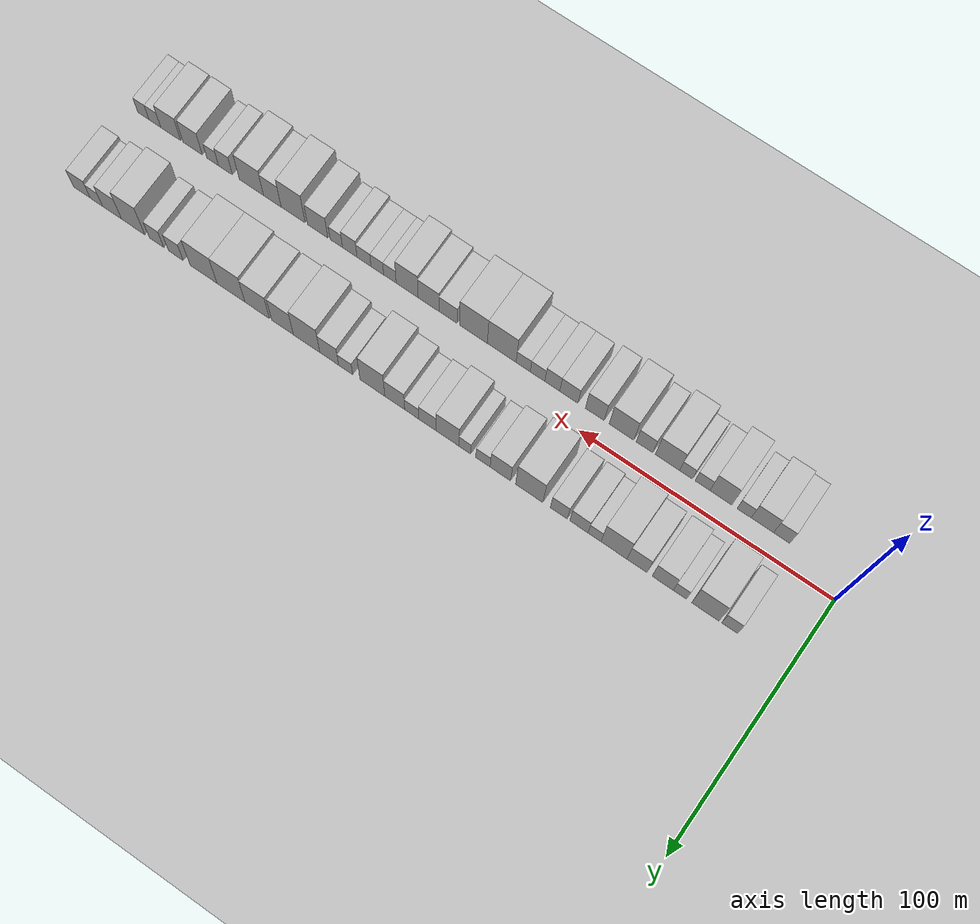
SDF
<?xml version="1.0" encoding="utf-8"?>

<sdf version="1.6">

   <world name="default">

      <gui fullscreen="0">

         <camera name="user_camera">

            <pose>-15 0 4.57585 0 0 0</pose>

            <view_controller>orbit</view_controller>

         </camera>

      </gui>

      <scene>

         <sky>

           <clouds>

             <speed>12</speed>

           </clouds>

         </sky>

         <ambient>0.4 0.4 0.4 1</ambient>

         <background>0.7 0.7 0.7 1</background>

         <shadows>1</shadows>

      </scene>

      <gravity>0 0 -9.8066</gravity>

      <magnetic_field>6e-06 2.3e-05 -4.2e-05</magnetic_field>

      <physics default="0" name="default_physics" type="ode">

         <ode>

            <solver>

               <type>quick</type>

               <iters>10</iters>

               <sor>1.0</sor>

               <use_dynamic_moi_rescaling>0</use_dynamic_moi_rescaling>

            </solver>

            <constraints>

               <cfm>0</cfm>

               <erp>0.2</erp>

               <contact_max_correcting_vel>100</contact_max_correcting_vel>

               <contact_surface_layer>0.001</contact_surface_layer>

            </constraints>

         </ode>

         <max_step_size>0.004</max_step_size>

         <real_time_factor>1</real_time_factor>

         <real_time_update_rate>250</real_time_update_rate>

      </physics>

      <light name="sun" type="directional">

         <cast_shadows>1</cast_shadows>

         <pose>0 0 10 0 0 0</pose>

         <diffuse>0.8 0.8 0.8 1</diffuse>

         <specular>0.2 0.2 0.2 1</specular>

         <attenuation>

            <range>1000</range>

            <constant>0.9</constant>

            <linear>0.01</linear>

            <quadratic>0.001</quadratic>

         </attenuation>

         <direction>-0.5 0.1 -0.9</direction>

      </light>

      <include>

         <name>ground_plane_1</name>

         <uri>model://HANNAS_ground_plane</uri>

         <pose>0 0 0  0 0 0</pose>

      </include>

      <include>

         <name>ground_plane_2</name>

         <uri>model://HANNAS_ground_plane</uri>

         <pose>100 0 0  0 0 0</pose>

      </include>

      <model name="building_1">

         <static>1</static>

         <pose frame="">23.0415 17.5000 0 0.000000 0.000000 1.570796</pose>

         <link name="link">

            <pose frame="">0 0 7.50 0 0 0</pose>

            <collision name="collision">

               <geometry>

                  <box>

                     <size>20.0000 6.0831 15.0000</size>

                  </box>

               </geometry>

               <max_contacts>10</max_contacts>

               <surface>

                  <contact>

                     <ode/>

                  </contact>

                  <bounce/>

                  <friction>

                     <torsional>

                        <ode/>

                     </torsional>

                     <ode/>

                  </friction>

               </surface>

            </collision>

            <visual name="visual">

               <cast_shadows>0</cast_shadows>

               <geometry>

                  <box>

                     <size>20.0000 6.0831 15.0000</size>

                  </box>

               </geometry>

               <material>

                  <script>

                     <uri>model://HANNAS_wall/materials/scripts</uri>

                     <uri>model://HANNAS_wall/materials/textures</uri>

                     <name>vrc/HANNAS_wall</name>

                  </script>

               </material>

            </visual>

            <self_collide>0</self_collide>

            <enable_wind>0</enable_wind>

            <kinematic>0</kinematic>

         </link>

      </model>

      <model name="building_2">

         <static>1</static>

         <pose frame="">32.3609 17.5000 0 0.000000 0.000000 1.570796</pose>

         <link name="link">

            <pose frame="">0 0 12.00 0 0 0</pose>

            <collision name="collision">

               <geometry>

                  <box>

                     <size>20.0000 10.5557 24.0000</size>

                  </box>

               </geometry>

               <max_contacts>10</max_contacts>

               <surface>

                  <contact>

                     <ode/>

                  </contact>

                  <bounce/>

                  <friction>

                     <torsional>

                        <ode/>

                     </torsional>

                     <ode/>

                  </friction>

               </surface>

            </collision>

            <visual name="visual">

               <cast_shadows>0</cast_shadows>

               <geometry>

                  <box>

                     <size>20.0000 10.5557 24.0000</size>

                  </box>

               </geometry>

               <material>

                  <script>

                     <uri>model://HANNAS_wall/materials/scripts</uri>

                     <uri>model://HANNAS_wall/materials/textures</uri>

                     <name>vrc/HANNAS_wall</name>

                  </script>

               </material>

            </visual>

            <self_collide>0</self_collide>

            <enable_wind>0</enable_wind>

            <kinematic>0</kinematic>

         </link>

      </model>

      <model name="building_3">

         <static>1</static>

         <pose frame="">42.2124 17.5000 0 0.000000 0.000000 1.570796</pose>

         <link name="link">

            <pose frame="">0 0 6.00 0 0 0</pose>

            <collision name="collision">

               <geometry>

                  <box>

                     <size>20.0000 5.1473 12.0000</size>

                  </box>

               </geometry>

               <max_contacts>10</max_contacts>

               <surface>

                  <contact>

                     <ode/>

                  </contact>

                  <bounce/>

                  <friction>

                     <torsional>

                        <ode/>

                     </torsional>

                     <ode/>

                  </friction>

               </surface>

            </collision>

            <visual name="visual">

               <cast_shadows>0</cast_shadows>

               <geometry>

                  <box>

                     <size>20.0000 5.1473 12.0000</size>

                  </box>

               </geometry>

               <material>

                  <script>

                     <uri>model://HANNAS_wall/materials/scripts</uri>

                     <uri>model://HANNAS_wall/materials/textures</uri>

                     <name>vrc/HANNAS_wall</name>

                  </script>

               </material>

            </visual>

            <self_collide>0</self_collide>

            <enable_wind>0</enable_wind>

            <kinematic>0</kinematic>

         </link>

      </model>

      <model name="building_4">

         <static>1</static>

         <pose frame="">48.9135 17.5000 0 0.000000 0.000000 1.570796</pose>

         <link name="link">

            <pose frame="">0 0 9.00 0 0 0</pose>

            <collision name="collision">

               <geometry>

                  <box>

                     <size>20.0000 8.2548 18.0000</size>

                  </box>

               </geometry>

               <max_contacts>10</max_contacts>

               <surface>

                  <contact>

                     <ode/>

                  </contact>

                  <bounce/>

                  <friction>

                     <torsional>

                        <ode/>

                     </torsional>

                     <ode/>

                  </friction>

               </surface>

            </collision>

            <visual name="visual">

               <cast_shadows>0</cast_shadows>

               <geometry>

                  <box>

                     <size>20.0000 8.2548 18.0000</size>

                  </box>

               </geometry>

               <material>

                  <script>

                     <uri>model://HANNAS_wall/materials/scripts</uri>

                     <uri>model://HANNAS_wall/materials/textures</uri>

                     <name>vrc/HANNAS_wall</name>

                  </script>

               </material>

            </visual>

            <self_collide>0</self_collide>

            <enable_wind>0</enable_wind>

            <kinematic>0</kinematic>

         </link>

      </model>

      <model name="building_5">

         <static>1</static>

         <pose frame="">58.9442 17.5000 0 0.000000 0.000000 1.570796</pose>

         <link name="link">

            <pose frame="">0 0 9.00 0 0 0</pose>

            <collision name="collision">

               <geometry>

                  <box>

                     <size>20.0000 7.8067 18.0000</size>

                  </box>

               </geometry>

               <max_contacts>10</max_contacts>

               <surface>

                  <contact>

                     <ode/>

                  </contact>

                  <bounce/>

                  <friction>

                     <torsional>

                        <ode/>

                     </torsional>

                     <ode/>

                  </friction>

               </surface>

            </collision>

            <visual name="visual">

               <cast_shadows>0</cast_shadows>

               <geometry>

                  <box>

                     <size>20.0000 7.8067 18.0000</size>

                  </box>

               </geometry>

               <material>

                  <script>

                     <uri>model://HANNAS_wall/materials/scripts</uri>

                     <uri>model://HANNAS_wall/materials/textures</uri>

                     <name>vrc/HANNAS_wall</name>

                  </script>

               </material>

            </visual>

            <self_collide>0</self_collide>

            <enable_wind>0</enable_wind>

            <kinematic>0</kinematic>

         </link>

      </model>

      <model name="building_6">

         <static>1</static>

         <pose frame="">68.0096 17.5000 0 0.000000 0.000000 1.570796</pose>

         <link name="link">

            <pose frame="">0 0 12.00 0 0 0</pose>

            <collision name="collision">

               <geometry>

                  <box>

                     <size>20.0000 10.3240 24.0000</size>

                  </box>

               </geometry>

               <max_contacts>10</max_contacts>

               <surface>

                  <contact>

                     <ode/>

                  </contact>

                  <bounce/>

                  <friction>

                     <torsional>

                        <ode/>

                     </torsional>

                     <ode/>

                  </friction>

               </surface>

            </collision>

            <visual name="visual">

               <cast_shadows>0</cast_shadows>

               <geometry>

                  <box>

                     <size>20.0000 10.3240 24.0000</size>

                  </box>

               </geometry>

               <material>

                  <script>

                     <uri>model://HANNAS_wall/materials/scripts</uri>

                     <uri>model://HANNAS_wall/materials/textures</uri>

                     <name>vrc/HANNAS_wall</name>

                  </script>

               </material>

            </visual>

            <self_collide>0</self_collide>

            <enable_wind>0</enable_wind>

            <kinematic>0</kinematic>

         </link>

      </model>

      <model name="building_7">

         <static>1</static>

         <pose frame="">75.7263 17.5000 0 0.000000 0.000000 1.570796</pose>

         <link name="link">

            <pose frame="">0 0 6.00 0 0 0</pose>

            <collision name="collision">

               <geometry>

                  <box>

                     <size>20.0000 5.1092 12.0000</size>

                  </box>

               </geometry>

               <max_contacts>10</max_contacts>

               <surface>

                  <contact>

                     <ode/>

                  </contact>

                  <bounce/>

                  <friction>

                     <torsional>

                        <ode/>

                     </torsional>

                     <ode/>

                  </friction>

               </surface>

            </collision>

            <visual name="visual">

               <cast_shadows>0</cast_shadows>

               <geometry>

                  <box>

                     <size>20.0000 5.1092 12.0000</size>

                  </box>

               </geometry>

               <material>

                  <script>

                     <uri>model://HANNAS_wall/materials/scripts</uri>

                     <uri>model://HANNAS_wall/materials/textures</uri>

                     <name>vrc/HANNAS_wall</name>

                  </script>

               </material>

            </visual>

            <self_collide>0</self_collide>

            <enable_wind>0</enable_wind>

            <kinematic>0</kinematic>

         </link>

      </model>

      <model name="building_8">

         <static>1</static>

         <pose frame="">81.8742 17.5000 0 0.000000 0.000000 1.570796</pose>

         <link name="link">

            <pose frame="">0 0 7.50 0 0 0</pose>

            <collision name="collision">

               <geometry>

                  <box>

                     <size>20.0000 7.1867 15.0000</size>

                  </box>

               </geometry>

               <max_contacts>10</max_contacts>

               <surface>

                  <contact>

                     <ode/>

                  </contact>

                  <bounce/>

                  <friction>

                     <torsional>

                        <ode/>

                     </torsional>

                     <ode/>

                  </friction>

               </surface>

            </collision>

            <visual name="visual">

               <cast_shadows>0</cast_shadows>

               <geometry>

                  <box>

                     <size>20.0000 7.1867 15.0000</size>

                  </box>

               </geometry>

               <material>

                  <script>

                     <uri>model://HANNAS_wall/materials/scripts</uri>

                     <uri>model://HANNAS_wall/materials/textures</uri>

                     <name>vrc/HANNAS_wall</name>

                  </script>

               </material>

            </visual>

            <self_collide>0</self_collide>

            <enable_wind>0</enable_wind>

            <kinematic>0</kinematic>

         </link>

      </model>

      <model name="building_9">

         <static>1</static>

         <pose frame="">89.8205 17.5000 0 0.000000 0.000000 1.570796</pose>

         <link name="link">

            <pose frame="">0 0 7.50 0 0 0</pose>

            <collision name="collision">

               <geometry>

                  <box>

                     <size>20.0000 6.7057 15.0000</size>

                  </box>

               </geometry>

               <max_contacts>10</max_contacts>

               <surface>

                  <contact>

                     <ode/>

                  </contact>

                  <bounce/>

                  <friction>

                     <torsional>

                        <ode/>

                     </torsional>

                     <ode/>

                  </friction>

               </surface>

            </collision>

            <visual name="visual">

               <cast_shadows>0</cast_shadows>

               <geometry>

                  <box>

                     <size>20.0000 6.7057 15.0000</size>

                  </box>

               </geometry>

               <material>

                  <script>

                     <uri>model://HANNAS_wall/materials/scripts</uri>

                     <uri>model://HANNAS_wall/materials/textures</uri>

                     <name>vrc/HANNAS_wall</name>

                  </script>

               </material>

            </visual>

            <self_collide>0</self_collide>

            <enable_wind>0</enable_wind>

            <kinematic>0</kinematic>

         </link>

      </model>

      <model name="building_10">

         <static>1</static>

         <pose frame="">101.6345 17.5000 0 0.000000 0.000000 1.570796</pose>

         <link name="link">

            <pose frame="">0 0 12.00 0 0 0</pose>

            <collision name="collision">

               <geometry>

                  <box>

                     <size>20.0000 10.9224 24.0000</size>

                  </box>

               </geometry>

               <max_contacts>10</max_contacts>

               <surface>

                  <contact>

                     <ode/>

                  </contact>

                  <bounce/>

                  <friction>

                     <torsional>

                        <ode/>

                     </torsional>

                     <ode/>

                  </friction>

               </surface>

            </collision>

            <visual name="visual">

               <cast_shadows>0</cast_shadows>

               <geometry>

                  <box>

                     <size>20.0000 10.9224 24.0000</size>

                  </box>

               </geometry>

               <material>

                  <script>

                     <uri>model://HANNAS_wall/materials/scripts</uri>

                     <uri>model://HANNAS_wall/materials/textures</uri>

                     <name>vrc/HANNAS_wall</name>

                  </script>

               </material>

            </visual>

            <self_collide>0</self_collide>

            <enable_wind>0</enable_wind>

            <kinematic>0</kinematic>

         </link>

      </model>

      <model name="building_11">

         <static>1</static>

         <pose frame="">113.2011 17.5000 0 0.000000 0.000000 1.570796</pose>

         <link name="link">

            <pose frame="">0 0 9.00 0 0 0</pose>

            <collision name="collision">

               <geometry>

                  <box>

                     <size>20.0000 8.2107 18.0000</size>

                  </box>

               </geometry>

               <max_contacts>10</max_contacts>

               <surface>

                  <contact>

                     <ode/>

                  </contact>

                  <bounce/>

                  <friction>

                     <torsional>

                        <ode/>

                     </torsional>

                     <ode/>

                  </friction>

               </surface>

            </collision>

            <visual name="visual">

               <cast_shadows>0</cast_shadows>

               <geometry>

                  <box>

                     <size>20.0000 8.2107 18.0000</size>

                  </box>

               </geometry>

               <material>

                  <script>

                     <uri>model://HANNAS_wall/materials/scripts</uri>

                     <uri>model://HANNAS_wall/materials/textures</uri>

                     <name>vrc/HANNAS_wall</name>

                  </script>

               </material>

            </visual>

            <self_collide>0</self_collide>

            <enable_wind>0</enable_wind>

            <kinematic>0</kinematic>

         </link>

      </model>

      <model name="building_12">

         <static>1</static>

         <pose frame="">120.2065 17.5000 0 0.000000 0.000000 1.570796</pose>

         <link name="link">

            <pose frame="">0 0 6.00 0 0 0</pose>

            <collision name="collision">

               <geometry>

                  <box>

                     <size>20.0000 5.8002 12.0000</size>

                  </box>

               </geometry>

               <max_contacts>10</max_contacts>

               <surface>

                  <contact>

                     <ode/>

                  </contact>

                  <bounce/>

                  <friction>

                     <torsional>

                        <ode/>

                     </torsional>

                     <ode/>

                  </friction>

               </surface>

            </collision>

            <visual name="visual">

               <cast_shadows>0</cast_shadows>

               <geometry>

                  <box>

                     <size>20.0000 5.8002 12.0000</size>

                  </box>

               </geometry>

               <material>

                  <script>

                     <uri>model://HANNAS_wall/materials/scripts</uri>

                     <uri>model://HANNAS_wall/materials/textures</uri>

                     <name>vrc/HANNAS_wall</name>

                  </script>

               </material>

            </visual>

            <self_collide>0</self_collide>

            <enable_wind>0</enable_wind>

            <kinematic>0</kinematic>

         </link>

      </model>

      <model name="building_13">

         <static>1</static>

         <pose frame="">127.5092 17.5000 0 0.000000 0.000000 1.570796</pose>

         <link name="link">

            <pose frame="">0 0 6.00 0 0 0</pose>

            <collision name="collision">

               <geometry>

                  <box>

                     <size>20.0000 4.8052 12.0000</size>

                  </box>

               </geometry>

               <max_contacts>10</max_contacts>

               <surface>

                  <contact>

                     <ode/>

                  </contact>

                  <bounce/>

                  <friction>

                     <torsional>

                        <ode/>

                     </torsional>

                     <ode/>

                  </friction>

               </surface>

            </collision>

            <visual name="visual">

               <cast_shadows>0</cast_shadows>

               <geometry>

                  <box>

                     <size>20.0000 4.8052 12.0000</size>

                  </box>

               </geometry>

               <material>

                  <script>

                     <uri>model://HANNAS_wall/materials/scripts</uri>

                     <uri>model://HANNAS_wall/materials/textures</uri>

                     <name>vrc/HANNAS_wall</name>

                  </script>

               </material>

            </visual>

            <self_collide>0</self_collide>

            <enable_wind>0</enable_wind>

            <kinematic>0</kinematic>

         </link>

      </model>

      <model name="building_14">

         <static>1</static>

         <pose frame="">134.5642 17.5000 0 0.000000 0.000000 1.570796</pose>

         <link name="link">

            <pose frame="">0 0 10.50 0 0 0</pose>

            <collision name="collision">

               <geometry>

                  <box>

                     <size>20.0000 9.3049 21.0000</size>

                  </box>

               </geometry>

               <max_contacts>10</max_contacts>

               <surface>

                  <contact>

                     <ode/>

                  </contact>

                  <bounce/>

                  <friction>

                     <torsional>

                        <ode/>

                     </torsional>

                     <ode/>

                  </friction>

               </surface>

            </collision>

            <visual name="visual">

               <cast_shadows>0</cast_shadows>

               <geometry>

                  <box>

                     <size>20.0000 9.3049 21.0000</size>

                  </box>

               </geometry>

               <material>

                  <script>

                     <uri>model://HANNAS_wall/materials/scripts</uri>

                     <uri>model://HANNAS_wall/materials/textures</uri>

                     <name>vrc/HANNAS_wall</name>

                  </script>

               </material>

            </visual>

            <self_collide>0</self_collide>

            <enable_wind>0</enable_wind>

            <kinematic>0</kinematic>

         </link>

      </model>

      <model name="building_15">

         <static>1</static>

         <pose frame="">142.7464 17.5000 0 0.000000 0.000000 1.570796</pose>

         <link name="link">

            <pose frame="">0 0 7.50 0 0 0</pose>

            <collision name="collision">

               <geometry>

                  <box>

                     <size>20.0000 7.0595 15.0000</size>

                  </box>

               </geometry>

               <max_contacts>10</max_contacts>

               <surface>

                  <contact>

                     <ode/>

                  </contact>

                  <bounce/>

                  <friction>

                     <torsional>

                        <ode/>

                     </torsional>

                     <ode/>

                  </friction>

               </surface>

            </collision>

            <visual name="visual">

               <cast_shadows>0</cast_shadows>

               <geometry>

                  <box>

                     <size>20.0000 7.0595 15.0000</size>

                  </box>

               </geometry>

               <material>

                  <script>

                     <uri>model://HANNAS_wall/materials/scripts</uri>

                     <uri>model://HANNAS_wall/materials/textures</uri>

                     <name>vrc/HANNAS_wall</name>

                  </script>

               </material>

            </visual>

            <self_collide>0</self_collide>

            <enable_wind>0</enable_wind>

            <kinematic>0</kinematic>

         </link>

      </model>

      <model name="building_16">

         <static>1</static>

         <pose frame="">149.1308 17.5000 0 0.000000 0.000000 1.570796</pose>

         <link name="link">

            <pose frame="">0 0 6.00 0 0 0</pose>

            <collision name="collision">

               <geometry>

                  <box>

                     <size>20.0000 5.7092 12.0000</size>

                  </box>

               </geometry>

               <max_contacts>10</max_contacts>

               <surface>

                  <contact>

                     <ode/>

                  </contact>

                  <bounce/>

                  <friction>

                     <torsional>

                        <ode/>

                     </torsional>

                     <ode/>

                  </friction>

               </surface>

            </collision>

            <visual name="visual">

               <cast_shadows>0</cast_shadows>

               <geometry>

                  <box>

                     <size>20.0000 5.7092 12.0000</size>

                  </box>

               </geometry>

               <material>

                  <script>

                     <uri>model://HANNAS_wall/materials/scripts</uri>

                     <uri>model://HANNAS_wall/materials/textures</uri>

                     <name>vrc/HANNAS_wall</name>

                  </script>

               </material>

            </visual>

            <self_collide>0</self_collide>

            <enable_wind>0</enable_wind>

            <kinematic>0</kinematic>

         </link>

      </model>

      <model name="building_17">

         <static>1</static>

         <pose frame="">156.0610 17.5000 0 0.000000 0.000000 1.570796</pose>

         <link name="link">

            <pose frame="">0 0 9.00 0 0 0</pose>

            <collision name="collision">

               <geometry>

                  <box>

                     <size>20.0000 8.1512 18.0000</size>

                  </box>

               </geometry>

               <max_contacts>10</max_contacts>

               <surface>

                  <contact>

                     <ode/>

                  </contact>

                  <bounce/>

                  <friction>

                     <torsional>

                        <ode/>

                     </torsional>

                     <ode/>

                  </friction>

               </surface>

            </collision>

            <visual name="visual">

               <cast_shadows>0</cast_shadows>

               <geometry>

                  <box>

                     <size>20.0000 8.1512 18.0000</size>

                  </box>

               </geometry>

               <material>

                  <script>

                     <uri>model://HANNAS_wall/materials/scripts</uri>

                     <uri>model://HANNAS_wall/materials/textures</uri>

                     <name>vrc/HANNAS_wall</name>

                  </script>

               </material>

            </visual>

            <self_collide>0</self_collide>

            <enable_wind>0</enable_wind>

            <kinematic>0</kinematic>

         </link>

      </model>

      <model name="building_18">

         <static>1</static>

         <pose frame="">165.2565 17.5000 0 0.000000 0.000000 1.570796</pose>

         <link name="link">

            <pose frame="">0 0 12.00 0 0 0</pose>

            <collision name="collision">

               <geometry>

                  <box>

                     <size>20.0000 10.2397 24.0000</size>

                  </box>

               </geometry>

               <max_contacts>10</max_contacts>

               <surface>

                  <contact>

                     <ode/>

                  </contact>

                  <bounce/>

                  <friction>

                     <torsional>

                        <ode/>

                     </torsional>

                     <ode/>

                  </friction>

               </surface>

            </collision>

            <visual name="visual">

               <cast_shadows>0</cast_shadows>

               <geometry>

                  <box>

                     <size>20.0000 10.2397 24.0000</size>

                  </box>

               </geometry>

               <material>

                  <script>

                     <uri>model://HANNAS_wall/materials/scripts</uri>

                     <uri>model://HANNAS_wall/materials/textures</uri>

                     <name>vrc/HANNAS_wall</name>

                  </script>

               </material>

            </visual>

            <self_collide>0</self_collide>

            <enable_wind>0</enable_wind>

            <kinematic>0</kinematic>

         </link>

      </model>

      <model name="building_19">

         <static>1</static>

         <pose frame="">176.2796 17.5000 0 0.000000 0.000000 1.570796</pose>

         <link name="link">

            <pose frame="">0 0 6.00 0 0 0</pose>

            <collision name="collision">

               <geometry>

                  <box>

                     <size>20.0000 5.8066 12.0000</size>

                  </box>

               </geometry>

               <max_contacts>10</max_contacts>

               <surface>

                  <contact>

                     <ode/>

                  </contact>

                  <bounce/>

                  <friction>

                     <torsional>

                        <ode/>

                     </torsional>

                     <ode/>

                  </friction>

               </surface>

            </collision>

            <visual name="visual">

               <cast_shadows>0</cast_shadows>

               <geometry>

                  <box>

                     <size>20.0000 5.8066 12.0000</size>

                  </box>

               </geometry>

               <material>

                  <script>

                     <uri>model://HANNAS_wall/materials/scripts</uri>

                     <uri>model://HANNAS_wall/materials/textures</uri>

                     <name>vrc/HANNAS_wall</name>

                  </script>

               </material>

            </visual>

            <self_collide>0</self_collide>

            <enable_wind>0</enable_wind>

            <kinematic>0</kinematic>

         </link>

      </model>

      <model name="building_20">

         <static>1</static>

         <pose frame="">183.0763 17.5000 0 0.000000 0.000000 1.570796</pose>

         <link name="link">

            <pose frame="">0 0 9.00 0 0 0</pose>

            <collision name="collision">

               <geometry>

                  <box>

                     <size>20.0000 7.7868 18.0000</size>

                  </box>

               </geometry>

               <max_contacts>10</max_contacts>

               <surface>

                  <contact>

                     <ode/>

                  </contact>

                  <bounce/>

                  <friction>

                     <torsional>

                        <ode/>

                     </torsional>

                     <ode/>

                  </friction>

               </surface>

            </collision>

            <visual name="visual">

               <cast_shadows>0</cast_shadows>

               <geometry>

                  <box>

                     <size>20.0000 7.7868 18.0000</size>

                  </box>

               </geometry>

               <material>

                  <script>

                     <uri>model://HANNAS_wall/materials/scripts</uri>

                     <uri>model://HANNAS_wall/materials/textures</uri>

                     <name>vrc/HANNAS_wall</name>

                  </script>

               </material>

            </visual>

            <self_collide>0</self_collide>

            <enable_wind>0</enable_wind>

            <kinematic>0</kinematic>

         </link>

      </model>

      <model name="building_21">

         <static>1</static>

         <pose frame="">192.4936 17.5000 0 0.000000 0.000000 1.570796</pose>

         <link name="link">

            <pose frame="">0 0 12.00 0 0 0</pose>

            <collision name="collision">

               <geometry>

                  <box>

                     <size>20.0000 11.0478 24.0000</size>

                  </box>

               </geometry>

               <max_contacts>10</max_contacts>

               <surface>

                  <contact>

                     <ode/>

                  </contact>

                  <bounce/>

                  <friction>

                     <torsional>

                        <ode/>

                     </torsional>

                     <ode/>

                  </friction>

               </surface>

            </collision>

            <visual name="visual">

               <cast_shadows>0</cast_shadows>

               <geometry>

                  <box>

                     <size>20.0000 11.0478 24.0000</size>

                  </box>

               </geometry>

               <material>

                  <script>

                     <uri>model://HANNAS_wall/materials/scripts</uri>

                     <uri>model://HANNAS_wall/materials/textures</uri>

                     <name>vrc/HANNAS_wall</name>

                  </script>

               </material>

            </visual>

            <self_collide>0</self_collide>

            <enable_wind>0</enable_wind>

            <kinematic>0</kinematic>

         </link>

      </model>

      <model name="building_22">

         <static>1</static>

         <pose frame="">202.5421 17.5000 0 0.000000 0.000000 1.570796</pose>

         <link name="link">

            <pose frame="">0 0 10.50 0 0 0</pose>

            <collision name="collision">

               <geometry>

                  <box>

                     <size>20.0000 9.0492 21.0000</size>

                  </box>

               </geometry>

               <max_contacts>10</max_contacts>

               <surface>

                  <contact>

                     <ode/>

                  </contact>

                  <bounce/>

                  <friction>

                     <torsional>

                        <ode/>

                     </torsional>

                     <ode/>

                  </friction>

               </surface>

            </collision>

            <visual name="visual">

               <cast_shadows>0</cast_shadows>

               <geometry>

                  <box>

                     <size>20.0000 9.0492 21.0000</size>

                  </box>

               </geometry>

               <material>

                  <script>

                     <uri>model://HANNAS_wall/materials/scripts</uri>

                     <uri>model://HANNAS_wall/materials/textures</uri>

                     <name>vrc/HANNAS_wall</name>

                  </script>

               </material>

            </visual>

            <self_collide>0</self_collide>

            <enable_wind>0</enable_wind>

            <kinematic>0</kinematic>

         </link>

      </model>

      <model name="building_23">

         <static>1</static>

         <pose frame="">213.2186 17.5000 0 0.000000 0.000000 1.570796</pose>

         <link name="link">

            <pose frame="">0 0 10.50 0 0 0</pose>

            <collision name="collision">

               <geometry>

                  <box>

                     <size>20.0000 10.3037 21.0000</size>

                  </box>

               </geometry>

               <max_contacts>10</max_contacts>

               <surface>

                  <contact>

                     <ode/>

                  </contact>

                  <bounce/>

                  <friction>

                     <torsional>

                        <ode/>

                     </torsional>

                     <ode/>

                  </friction>

               </surface>

            </collision>

            <visual name="visual">

               <cast_shadows>0</cast_shadows>

               <geometry>

                  <box>

                     <size>20.0000 10.3037 21.0000</size>

                  </box>

               </geometry>

               <material>

                  <script>

                     <uri>model://HANNAS_wall/materials/scripts</uri>

                     <uri>model://HANNAS_wall/materials/textures</uri>

                     <name>vrc/HANNAS_wall</name>

                  </script>

               </material>

            </visual>

            <self_collide>0</self_collide>

            <enable_wind>0</enable_wind>

            <kinematic>0</kinematic>

         </link>

      </model>

      <model name="building_24">

         <static>1</static>

         <pose frame="">224.2956 17.5000 0 0.000000 0.000000 1.570796</pose>

         <link name="link">

            <pose frame="">0 0 12.00 0 0 0</pose>

            <collision name="collision">

               <geometry>

                  <box>

                     <size>20.0000 11.8503 24.0000</size>

                  </box>

               </geometry>

               <max_contacts>10</max_contacts>

               <surface>

                  <contact>

                     <ode/>

                  </contact>

                  <bounce/>

                  <friction>

                     <torsional>

                        <ode/>

                     </torsional>

                     <ode/>

                  </friction>

               </surface>

            </collision>

            <visual name="visual">

               <cast_shadows>0</cast_shadows>

               <geometry>

                  <box>

                     <size>20.0000 11.8503 24.0000</size>

                  </box>

               </geometry>

               <material>

                  <script>

                     <uri>model://HANNAS_wall/materials/scripts</uri>

                     <uri>model://HANNAS_wall/materials/textures</uri>

                     <name>vrc/HANNAS_wall</name>

                  </script>

               </material>

            </visual>

            <self_collide>0</self_collide>

            <enable_wind>0</enable_wind>

            <kinematic>0</kinematic>

         </link>

      </model>

      <model name="building_25">

         <static>1</static>

         <pose frame="">235.9127 17.5000 0 0.000000 0.000000 1.570796</pose>

         <link name="link">

            <pose frame="">0 0 12.00 0 0 0</pose>

            <collision name="collision">

               <geometry>

                  <box>

                     <size>20.0000 11.3839 24.0000</size>

                  </box>

               </geometry>

               <max_contacts>10</max_contacts>

               <surface>

                  <contact>

                     <ode/>

                  </contact>

                  <bounce/>

                  <friction>

                     <torsional>

                        <ode/>

                     </torsional>

                     <ode/>

                  </friction>

               </surface>

            </collision>

            <visual name="visual">

               <cast_shadows>0</cast_shadows>

               <geometry>

                  <box>

                     <size>20.0000 11.3839 24.0000</size>

                  </box>

               </geometry>

               <material>

                  <script>

                     <uri>model://HANNAS_wall/materials/scripts</uri>

                     <uri>model://HANNAS_wall/materials/textures</uri>

                     <name>vrc/HANNAS_wall</name>

                  </script>

               </material>

            </visual>

            <self_collide>0</self_collide>

            <enable_wind>0</enable_wind>

            <kinematic>0</kinematic>

         </link>

      </model>

      <model name="building_26">

         <static>1</static>

         <pose frame="">247.7587 17.5000 0 0.000000 0.000000 1.570796</pose>

         <link name="link">

            <pose frame="">0 0 7.50 0 0 0</pose>

            <collision name="collision">

               <geometry>

                  <box>

                     <size>20.0000 6.3081 15.0000</size>

                  </box>

               </geometry>

               <max_contacts>10</max_contacts>

               <surface>

                  <contact>

                     <ode/>

                  </contact>

                  <bounce/>

                  <friction>

                     <torsional>

                        <ode/>

                     </torsional>

                     <ode/>

                  </friction>

               </surface>

            </collision>

            <visual name="visual">

               <cast_shadows>0</cast_shadows>

               <geometry>

                  <box>

                     <size>20.0000 6.3081 15.0000</size>

                  </box>

               </geometry>

               <material>

                  <script>

                     <uri>model://HANNAS_wall/materials/scripts</uri>

                     <uri>model://HANNAS_wall/materials/textures</uri>

                     <name>vrc/HANNAS_wall</name>

                  </script>

               </material>

            </visual>

            <self_collide>0</self_collide>

            <enable_wind>0</enable_wind>

            <kinematic>0</kinematic>

         </link>

      </model>

      <model name="building_27">

         <static>1</static>

         <pose frame="">255.9973 17.5000 0 0.000000 0.000000 1.570796</pose>

         <link name="link">

            <pose frame="">0 0 7.50 0 0 0</pose>

            <collision name="collision">

               <geometry>

                  <box>

                     <size>20.0000 6.1690 15.0000</size>

                  </box>

               </geometry>

               <max_contacts>10</max_contacts>

               <surface>

                  <contact>

                     <ode/>

                  </contact>

                  <bounce/>

                  <friction>

                     <torsional>

                        <ode/>

                     </torsional>

                     <ode/>

                  </friction>

               </surface>

            </collision>

            <visual name="visual">

               <cast_shadows>0</cast_shadows>

               <geometry>

                  <box>

                     <size>20.0000 6.1690 15.0000</size>

                  </box>

               </geometry>

               <material>

                  <script>

                     <uri>model://HANNAS_wall/materials/scripts</uri>

                     <uri>model://HANNAS_wall/materials/textures</uri>

                     <name>vrc/HANNAS_wall</name>

                  </script>

               </material>

            </visual>

            <self_collide>0</self_collide>

            <enable_wind>0</enable_wind>

            <kinematic>0</kinematic>

         </link>

      </model>

      <model name="building_28">

         <static>1</static>

         <pose frame="">266.0833 17.5000 0 0.000000 0.000000 1.570796</pose>

         <link name="link">

            <pose frame="">0 0 12.00 0 0 0</pose>

            <collision name="collision">

               <geometry>

                  <box>

                     <size>20.0000 10.0030 24.0000</size>

                  </box>

               </geometry>

               <max_contacts>10</max_contacts>

               <surface>

                  <contact>

                     <ode/>

                  </contact>

                  <bounce/>

                  <friction>

                     <torsional>

                        <ode/>

                     </torsional>

                     <ode/>

                  </friction>

               </surface>

            </collision>

            <visual name="visual">

               <cast_shadows>0</cast_shadows>

               <geometry>

                  <box>

                     <size>20.0000 10.0030 24.0000</size>

                  </box>

               </geometry>

               <material>

                  <script>

                     <uri>model://HANNAS_wall/materials/scripts</uri>

                     <uri>model://HANNAS_wall/materials/textures</uri>

                     <name>vrc/HANNAS_wall</name>

                  </script>

               </material>

            </visual>

            <self_collide>0</self_collide>

            <enable_wind>0</enable_wind>

            <kinematic>0</kinematic>

         </link>

      </model>

      <model name="building_29">

         <static>1</static>

         <pose frame="">275.2106 17.5000 0 0.000000 0.000000 1.570796</pose>

         <link name="link">

            <pose frame="">0 0 9.00 0 0 0</pose>

            <collision name="collision">

               <geometry>

                  <box>

                     <size>20.0000 8.2515 18.0000</size>

                  </box>

               </geometry>

               <max_contacts>10</max_contacts>

               <surface>

                  <contact>

                     <ode/>

                  </contact>

                  <bounce/>

                  <friction>

                     <torsional>

                        <ode/>

                     </torsional>

                     <ode/>

                  </friction>

               </surface>

            </collision>

            <visual name="visual">

               <cast_shadows>0</cast_shadows>

               <geometry>

                  <box>

                     <size>20.0000 8.2515 18.0000</size>

                  </box>

               </geometry>

               <material>

                  <script>

                     <uri>model://HANNAS_wall/materials/scripts</uri>

                     <uri>model://HANNAS_wall/materials/textures</uri>

                     <name>vrc/HANNAS_wall</name>

                  </script>

               </material>

            </visual>

            <self_collide>0</self_collide>

            <enable_wind>0</enable_wind>

            <kinematic>0</kinematic>

         </link>

      </model>

      <model name="building_30">

         <static>1</static>

         <pose frame="">281.9641 17.5000 0 0.000000 0.000000 1.570796</pose>

         <link name="link">

            <pose frame="">0 0 6.00 0 0 0</pose>

            <collision name="collision">

               <geometry>

                  <box>

                     <size>20.0000 5.2556 12.0000</size>

                  </box>

               </geometry>

               <max_contacts>10</max_contacts>

               <surface>

                  <contact>

                     <ode/>

                  </contact>

                  <bounce/>

                  <friction>

                     <torsional>

                        <ode/>

                     </torsional>

                     <ode/>

                  </friction>

               </surface>

            </collision>

            <visual name="visual">

               <cast_shadows>0</cast_shadows>

               <geometry>

                  <box>

                     <size>20.0000 5.2556 12.0000</size>

                  </box>

               </geometry>

               <material>

                  <script>

                     <uri>model://HANNAS_wall/materials/scripts</uri>

                     <uri>model://HANNAS_wall/materials/textures</uri>

                     <name>vrc/HANNAS_wall</name>

                  </script>

               </material>

            </visual>

            <self_collide>0</self_collide>

            <enable_wind>0</enable_wind>

            <kinematic>0</kinematic>

         </link>

      </model>

      <model name="building_31">

         <static>1</static>

         <pose frame="">288.2241 17.5000 0 0.000000 0.000000 1.570796</pose>

         <link name="link">

            <pose frame="">0 0 7.50 0 0 0</pose>

            <collision name="collision">

               <geometry>

                  <box>

                     <size>20.0000 7.2644 15.0000</size>

                  </box>

               </geometry>

               <max_contacts>10</max_contacts>

               <surface>

                  <contact>

                     <ode/>

                  </contact>

                  <bounce/>

                  <friction>

                     <torsional>

                        <ode/>

                     </torsional>

                     <ode/>

                  </friction>

               </surface>

            </collision>

            <visual name="visual">

               <cast_shadows>0</cast_shadows>

               <geometry>

                  <box>

                     <size>20.0000 7.2644 15.0000</size>

                  </box>

               </geometry>

               <material>

                  <script>

                     <uri>model://HANNAS_wall/materials/scripts</uri>

                     <uri>model://HANNAS_wall/materials/textures</uri>

                     <name>vrc/HANNAS_wall</name>

                  </script>

               </material>

            </visual>

            <self_collide>0</self_collide>

            <enable_wind>0</enable_wind>

            <kinematic>0</kinematic>

         </link>

      </model>

      <model name="building_32">

         <static>1</static>

         <pose frame="">25.1367 -17.5000 0 0.000000 0.000000 1.570796</pose>

         <link name="link">

            <pose frame="">0 0 7.50 0 0 0</pose>

            <collision name="collision">

               <geometry>

                  <box>

                     <size>20.0000 6.2735 15.0000</size>

                  </box>

               </geometry>

               <max_contacts>10</max_contacts>

               <surface>

                  <contact>

                     <ode/>

                  </contact>

                  <bounce/>

                  <friction>

                     <torsional>

                        <ode/>

                     </torsional>

                     <ode/>

                  </friction>

               </surface>

            </collision>

            <visual name="visual">

               <cast_shadows>0</cast_shadows>

               <geometry>

                  <box>

                     <size>20.0000 6.2735 15.0000</size>

                  </box>

               </geometry>

               <material>

                  <script>

                     <uri>model://HANNAS_wall/materials/scripts</uri>

                     <uri>model://HANNAS_wall/materials/textures</uri>

                     <name>vrc/HANNAS_wall</name>

                  </script>

               </material>

            </visual>

            <self_collide>0</self_collide>

            <enable_wind>0</enable_wind>

            <kinematic>0</kinematic>

         </link>

      </model>

      <model name="building_33">

         <static>1</static>

         <pose frame="">32.6409 -17.5000 0 0.000000 0.000000 1.570796</pose>

         <link name="link">

            <pose frame="">0 0 9.00 0 0 0</pose>

            <collision name="collision">

               <geometry>

                  <box>

                     <size>20.0000 8.7348 18.0000</size>

                  </box>

               </geometry>

               <max_contacts>10</max_contacts>

               <surface>

                  <contact>

                     <ode/>

                  </contact>

                  <bounce/>

                  <friction>

                     <torsional>

                        <ode/>

                     </torsional>

                     <ode/>

                  </friction>

               </surface>

            </collision>

            <visual name="visual">

               <cast_shadows>0</cast_shadows>

               <geometry>

                  <box>

                     <size>20.0000 8.7348 18.0000</size>

                  </box>

               </geometry>

               <material>

                  <script>

                     <uri>model://HANNAS_wall/materials/scripts</uri>

                     <uri>model://HANNAS_wall/materials/textures</uri>

                     <name>vrc/HANNAS_wall</name>

                  </script>

               </material>

            </visual>

            <self_collide>0</self_collide>

            <enable_wind>0</enable_wind>

            <kinematic>0</kinematic>

         </link>

      </model>

      <model name="building_34">

         <static>1</static>

         <pose frame="">39.7493 -17.5000 0 0.000000 0.000000 1.570796</pose>

         <link name="link">

            <pose frame="">0 0 6.00 0 0 0</pose>

            <collision name="collision">

               <geometry>

                  <box>

                     <size>20.0000 5.4820 12.0000</size>

                  </box>

               </geometry>

               <max_contacts>10</max_contacts>

               <surface>

                  <contact>

                     <ode/>

                  </contact>

                  <bounce/>

                  <friction>

                     <torsional>

                        <ode/>

                     </torsional>

                     <ode/>

                  </friction>

               </surface>

            </collision>

            <visual name="visual">

               <cast_shadows>0</cast_shadows>

               <geometry>

                  <box>

                     <size>20.0000 5.4820 12.0000</size>

                  </box>

               </geometry>

               <material>

                  <script>

                     <uri>model://HANNAS_wall/materials/scripts</uri>

                     <uri>model://HANNAS_wall/materials/textures</uri>

                     <name>vrc/HANNAS_wall</name>

                  </script>

               </material>

            </visual>

            <self_collide>0</self_collide>

            <enable_wind>0</enable_wind>

            <kinematic>0</kinematic>

         </link>

      </model>

      <model name="building_35">

         <static>1</static>

         <pose frame="">48.8009 -17.5000 0 0.000000 0.000000 1.570796</pose>

         <link name="link">

            <pose frame="">0 0 10.50 0 0 0</pose>

            <collision name="collision">

               <geometry>

                  <box>

                     <size>20.0000 8.6214 21.0000</size>

                  </box>

               </geometry>

               <max_contacts>10</max_contacts>

               <surface>

                  <contact>

                     <ode/>

                  </contact>

                  <bounce/>

                  <friction>

                     <torsional>

                        <ode/>

                     </torsional>

                     <ode/>

                  </friction>

               </surface>

            </collision>

            <visual name="visual">

               <cast_shadows>0</cast_shadows>

               <geometry>

                  <box>

                     <size>20.0000 8.6214 21.0000</size>

                  </box>

               </geometry>

               <material>

                  <script>

                     <uri>model://HANNAS_wall/materials/scripts</uri>

                     <uri>model://HANNAS_wall/materials/textures</uri>

                     <name>vrc/HANNAS_wall</name>

                  </script>

               </material>

            </visual>

            <self_collide>0</self_collide>

            <enable_wind>0</enable_wind>

            <kinematic>0</kinematic>

         </link>

      </model>

      <model name="building_36">

         <static>1</static>

         <pose frame="">56.0517 -17.5000 0 0.000000 0.000000 1.570796</pose>

         <link name="link">

            <pose frame="">0 0 6.00 0 0 0</pose>

            <collision name="collision">

               <geometry>

                  <box>

                     <size>20.0000 5.8803 12.0000</size>

                  </box>

               </geometry>

               <max_contacts>10</max_contacts>

               <surface>

                  <contact>

                     <ode/>

                  </contact>

                  <bounce/>

                  <friction>

                     <torsional>

                        <ode/>

                     </torsional>

                     <ode/>

                  </friction>

               </surface>

            </collision>

            <visual name="visual">

               <cast_shadows>0</cast_shadows>

               <geometry>

                  <box>

                     <size>20.0000 5.8803 12.0000</size>

                  </box>

               </geometry>

               <material>

                  <script>

                     <uri>model://HANNAS_wall/materials/scripts</uri>

                     <uri>model://HANNAS_wall/materials/textures</uri>

                     <name>vrc/HANNAS_wall</name>

                  </script>

               </material>

            </visual>

            <self_collide>0</self_collide>

            <enable_wind>0</enable_wind>

            <kinematic>0</kinematic>

         </link>

      </model>

      <model name="building_37">

         <static>1</static>

         <pose frame="">62.5521 -17.5000 0 0.000000 0.000000 1.570796</pose>

         <link name="link">

            <pose frame="">0 0 6.00 0 0 0</pose>

            <collision name="collision">

               <geometry>

                  <box>

                     <size>20.0000 5.1204 12.0000</size>

                  </box>

               </geometry>

               <max_contacts>10</max_contacts>

               <surface>

                  <contact>

                     <ode/>

                  </contact>

                  <bounce/>

                  <friction>

                     <torsional>

                        <ode/>

                     </torsional>

                     <ode/>

                  </friction>

               </surface>

            </collision>

            <visual name="visual">

               <cast_shadows>0</cast_shadows>

               <geometry>

                  <box>

                     <size>20.0000 5.1204 12.0000</size>

                  </box>

               </geometry>

               <material>

                  <script>

                     <uri>model://HANNAS_wall/materials/scripts</uri>

                     <uri>model://HANNAS_wall/materials/textures</uri>

                     <name>vrc/HANNAS_wall</name>

                  </script>

               </material>

            </visual>

            <self_collide>0</self_collide>

            <enable_wind>0</enable_wind>

            <kinematic>0</kinematic>

         </link>

      </model>

      <model name="building_38">

         <static>1</static>

         <pose frame="">69.9210 -17.5000 0 0.000000 0.000000 1.570796</pose>

         <link name="link">

            <pose frame="">0 0 10.50 0 0 0</pose>

            <collision name="collision">

               <geometry>

                  <box>

                     <size>20.0000 9.6175 21.0000</size>

                  </box>

               </geometry>

               <max_contacts>10</max_contacts>

               <surface>

                  <contact>

                     <ode/>

                  </contact>

                  <bounce/>

                  <friction>

                     <torsional>

                        <ode/>

                     </torsional>

                     <ode/>

                  </friction>

               </surface>

            </collision>

            <visual name="visual">

               <cast_shadows>0</cast_shadows>

               <geometry>

                  <box>

                     <size>20.0000 9.6175 21.0000</size>

                  </box>

               </geometry>

               <material>

                  <script>

                     <uri>model://HANNAS_wall/materials/scripts</uri>

                     <uri>model://HANNAS_wall/materials/textures</uri>

                     <name>vrc/HANNAS_wall</name>

                  </script>

               </material>

            </visual>

            <self_collide>0</self_collide>

            <enable_wind>0</enable_wind>

            <kinematic>0</kinematic>

         </link>

      </model>

      <model name="building_39">

         <static>1</static>

         <pose frame="">79.0266 -17.5000 0 0.000000 0.000000 1.570796</pose>

         <link name="link">

            <pose frame="">0 0 7.50 0 0 0</pose>

            <collision name="collision">

               <geometry>

                  <box>

                     <size>20.0000 6.5937 15.0000</size>

                  </box>

               </geometry>

               <max_contacts>10</max_contacts>

               <surface>

                  <contact>

                     <ode/>

                  </contact>

                  <bounce/>

                  <friction>

                     <torsional>

                        <ode/>

                     </torsional>

                     <ode/>

                  </friction>

               </surface>

            </collision>

            <visual name="visual">

               <cast_shadows>0</cast_shadows>

               <geometry>

                  <box>

                     <size>20.0000 6.5937 15.0000</size>

                  </box>

               </geometry>

               <material>

                  <script>

                     <uri>model://HANNAS_wall/materials/scripts</uri>

                     <uri>model://HANNAS_wall/materials/textures</uri>

                     <name>vrc/HANNAS_wall</name>

                  </script>

               </material>

            </visual>

            <self_collide>0</self_collide>

            <enable_wind>0</enable_wind>

            <kinematic>0</kinematic>

         </link>

      </model>

      <model name="building_40">

         <static>1</static>

         <pose frame="">88.2619 -17.5000 0 0.000000 0.000000 1.570796</pose>

         <link name="link">

            <pose frame="">0 0 10.50 0 0 0</pose>

            <collision name="collision">

               <geometry>

                  <box>

                     <size>20.0000 9.8768 21.0000</size>

                  </box>

               </geometry>

               <max_contacts>10</max_contacts>

               <surface>

                  <contact>

                     <ode/>

                  </contact>

                  <bounce/>

                  <friction>

                     <torsional>

                        <ode/>

                     </torsional>

                     <ode/>

                  </friction>

               </surface>

            </collision>

            <visual name="visual">

               <cast_shadows>0</cast_shadows>

               <geometry>

                  <box>

                     <size>20.0000 9.8768 21.0000</size>

                  </box>

               </geometry>

               <material>

                  <script>

                     <uri>model://HANNAS_wall/materials/scripts</uri>

                     <uri>model://HANNAS_wall/materials/textures</uri>

                     <name>vrc/HANNAS_wall</name>

                  </script>

               </material>

            </visual>

            <self_collide>0</self_collide>

            <enable_wind>0</enable_wind>

            <kinematic>0</kinematic>

         </link>

      </model>

      <model name="building_41">

         <static>1</static>

         <pose frame="">98.9503 -17.5000 0 0.000000 0.000000 1.570796</pose>

         <link name="link">

            <pose frame="">0 0 9.00 0 0 0</pose>

            <collision name="collision">

               <geometry>

                  <box>

                     <size>20.0000 7.5000 18.0000</size>

                  </box>

               </geometry>

               <max_contacts>10</max_contacts>

               <surface>

                  <contact>

                     <ode/>

                  </contact>

                  <bounce/>

                  <friction>

                     <torsional>

                        <ode/>

                     </torsional>

                     <ode/>

                  </friction>

               </surface>

            </collision>

            <visual name="visual">

               <cast_shadows>0</cast_shadows>

               <geometry>

                  <box>

                     <size>20.0000 7.5000 18.0000</size>

                  </box>

               </geometry>

               <material>

                  <script>

                     <uri>model://HANNAS_wall/materials/scripts</uri>

                     <uri>model://HANNAS_wall/materials/textures</uri>

                     <name>vrc/HANNAS_wall</name>

                  </script>

               </material>

            </visual>

            <self_collide>0</self_collide>

            <enable_wind>0</enable_wind>

            <kinematic>0</kinematic>

         </link>

      </model>

      <model name="building_42">

         <static>1</static>

         <pose frame="">109.3816 -17.5000 0 0.000000 0.000000 1.570796</pose>

         <link name="link">

            <pose frame="">0 0 7.50 0 0 0</pose>

            <collision name="collision">

               <geometry>

                  <box>

                     <size>20.0000 7.3627 15.0000</size>

                  </box>

               </geometry>

               <max_contacts>10</max_contacts>

               <surface>

                  <contact>

                     <ode/>

                  </contact>

                  <bounce/>

                  <friction>

                     <torsional>

                        <ode/>

                     </torsional>

                     <ode/>

                  </friction>

               </surface>

            </collision>

            <visual name="visual">

               <cast_shadows>0</cast_shadows>

               <geometry>

                  <box>

                     <size>20.0000 7.3627 15.0000</size>

                  </box>

               </geometry>

               <material>

                  <script>

                     <uri>model://HANNAS_wall/materials/scripts</uri>

                     <uri>model://HANNAS_wall/materials/textures</uri>

                     <name>vrc/HANNAS_wall</name>

                  </script>

               </material>

            </visual>

            <self_collide>0</self_collide>

            <enable_wind>0</enable_wind>

            <kinematic>0</kinematic>

         </link>

      </model>

      <model name="building_43">

         <static>1</static>

         <pose frame="">116.0820 -17.5000 0 0.000000 0.000000 1.570796</pose>

         <link name="link">

            <pose frame="">0 0 7.50 0 0 0</pose>

            <collision name="collision">

               <geometry>

                  <box>

                     <size>20.0000 6.0380 15.0000</size>

                  </box>

               </geometry>

               <max_contacts>10</max_contacts>

               <surface>

                  <contact>

                     <ode/>

                  </contact>

                  <bounce/>

                  <friction>

                     <torsional>

                        <ode/>

                     </torsional>

                     <ode/>

                  </friction>

               </surface>

            </collision>

            <visual name="visual">

               <cast_shadows>0</cast_shadows>

               <geometry>

                  <box>

                     <size>20.0000 6.0380 15.0000</size>

                  </box>

               </geometry>

               <material>

                  <script>

                     <uri>model://HANNAS_wall/materials/scripts</uri>

                     <uri>model://HANNAS_wall/materials/textures</uri>

                     <name>vrc/HANNAS_wall</name>

                  </script>

               </material>

            </visual>

            <self_collide>0</self_collide>

            <enable_wind>0</enable_wind>

            <kinematic>0</kinematic>

         </link>

      </model>

      <model name="building_44">

         <static>1</static>

         <pose frame="">122.0610 -17.5000 0 0.000000 0.000000 1.570796</pose>

         <link name="link">

            <pose frame="">0 0 6.00 0 0 0</pose>

            <collision name="collision">

               <geometry>

                  <box>

                     <size>20.0000 5.9201 12.0000</size>

                  </box>

               </geometry>

               <max_contacts>10</max_contacts>

               <surface>

                  <contact>

                     <ode/>

                  </contact>

                  <bounce/>

                  <friction>

                     <torsional>

                        <ode/>

                     </torsional>

                     <ode/>

                  </friction>

               </surface>

            </collision>

            <visual name="visual">

               <cast_shadows>0</cast_shadows>

               <geometry>

                  <box>

                     <size>20.0000 5.9201 12.0000</size>

                  </box>

               </geometry>

               <material>

                  <script>

                     <uri>model://HANNAS_wall/materials/scripts</uri>

                     <uri>model://HANNAS_wall/materials/textures</uri>

                     <name>vrc/HANNAS_wall</name>

                  </script>

               </material>

            </visual>

            <self_collide>0</self_collide>

            <enable_wind>0</enable_wind>

            <kinematic>0</kinematic>

         </link>

      </model>

      <model name="building_45">

         <static>1</static>

         <pose frame="">127.9046 -17.5000 0 0.000000 0.000000 1.570796</pose>

         <link name="link">

            <pose frame="">0 0 6.00 0 0 0</pose>

            <collision name="collision">

               <geometry>

                  <box>

                     <size>20.0000 5.7670 12.0000</size>

                  </box>

               </geometry>

               <max_contacts>10</max_contacts>

               <surface>

                  <contact>

                     <ode/>

                  </contact>

                  <bounce/>

                  <friction>

                     <torsional>

                        <ode/>

                     </torsional>

                     <ode/>

                  </friction>

               </surface>

            </collision>

            <visual name="visual">

               <cast_shadows>0</cast_shadows>

               <geometry>

                  <box>

                     <size>20.0000 5.7670 12.0000</size>

                  </box>

               </geometry>

               <material>

                  <script>

                     <uri>model://HANNAS_wall/materials/scripts</uri>

                     <uri>model://HANNAS_wall/materials/textures</uri>

                     <name>vrc/HANNAS_wall</name>

                  </script>

               </material>

            </visual>

            <self_collide>0</self_collide>

            <enable_wind>0</enable_wind>

            <kinematic>0</kinematic>

         </link>

      </model>

      <model name="building_46">

         <static>1</static>

         <pose frame="">136.6797 -17.5000 0 0.000000 0.000000 1.570796</pose>

         <link name="link">

            <pose frame="">0 0 12.00 0 0 0</pose>

            <collision name="collision">

               <geometry>

                  <box>

                     <size>20.0000 11.7832 24.0000</size>

                  </box>

               </geometry>

               <max_contacts>10</max_contacts>

               <surface>

                  <contact>

                     <ode/>

                  </contact>

                  <bounce/>

                  <friction>

                     <torsional>

                        <ode/>

                     </torsional>

                     <ode/>

                  </friction>

               </surface>

            </collision>

            <visual name="visual">

               <cast_shadows>0</cast_shadows>

               <geometry>

                  <box>

                     <size>20.0000 11.7832 24.0000</size>

                  </box>

               </geometry>

               <material>

                  <script>

                     <uri>model://HANNAS_wall/materials/scripts</uri>

                     <uri>model://HANNAS_wall/materials/textures</uri>

                     <name>vrc/HANNAS_wall</name>

                  </script>

               </material>

            </visual>

            <self_collide>0</self_collide>

            <enable_wind>0</enable_wind>

            <kinematic>0</kinematic>

         </link>

      </model>

      <model name="building_47">

         <static>1</static>

         <pose frame="">148.2702 -17.5000 0 0.000000 0.000000 1.570796</pose>

         <link name="link">

            <pose frame="">0 0 12.00 0 0 0</pose>

            <collision name="collision">

               <geometry>

                  <box>

                     <size>20.0000 11.3979 24.0000</size>

                  </box>

               </geometry>

               <max_contacts>10</max_contacts>

               <surface>

                  <contact>

                     <ode/>

                  </contact>

                  <bounce/>

                  <friction>

                     <torsional>

                        <ode/>

                     </torsional>

                     <ode/>

                  </friction>

               </surface>

            </collision>

            <visual name="visual">

               <cast_shadows>0</cast_shadows>

               <geometry>

                  <box>

                     <size>20.0000 11.3979 24.0000</size>

                  </box>

               </geometry>

               <material>

                  <script>

                     <uri>model://HANNAS_wall/materials/scripts</uri>

                     <uri>model://HANNAS_wall/materials/textures</uri>

                     <name>vrc/HANNAS_wall</name>

                  </script>

               </material>

            </visual>

            <self_collide>0</self_collide>

            <enable_wind>0</enable_wind>

            <kinematic>0</kinematic>

         </link>

      </model>

      <model name="building_48">

         <static>1</static>

         <pose frame="">158.7032 -17.5000 0 0.000000 0.000000 1.570796</pose>

         <link name="link">

            <pose frame="">0 0 7.50 0 0 0</pose>

            <collision name="collision">

               <geometry>

                  <box>

                     <size>20.0000 7.4682 15.0000</size>

                  </box>

               </geometry>

               <max_contacts>10</max_contacts>

               <surface>

                  <contact>

                     <ode/>

                  </contact>

                  <bounce/>

                  <friction>

                     <torsional>

                        <ode/>

                     </torsional>

                     <ode/>

                  </friction>

               </surface>

            </collision>

            <visual name="visual">

               <cast_shadows>0</cast_shadows>

               <geometry>

                  <box>

                     <size>20.0000 7.4682 15.0000</size>

                  </box>

               </geometry>

               <material>

                  <script>

                     <uri>model://HANNAS_wall/materials/scripts</uri>

                     <uri>model://HANNAS_wall/materials/textures</uri>

                     <name>vrc/HANNAS_wall</name>

                  </script>

               </material>

            </visual>

            <self_collide>0</self_collide>

            <enable_wind>0</enable_wind>

            <kinematic>0</kinematic>

         </link>

      </model>

      <model name="building_49">

         <static>1</static>

         <pose frame="">166.7735 -17.5000 0 0.000000 0.000000 1.570796</pose>

         <link name="link">

            <pose frame="">0 0 9.00 0 0 0</pose>

            <collision name="collision">

               <geometry>

                  <box>

                     <size>20.0000 8.6723 18.0000</size>

                  </box>

               </geometry>

               <max_contacts>10</max_contacts>

               <surface>

                  <contact>

                     <ode/>

                  </contact>

                  <bounce/>

                  <friction>

                     <torsional>

                        <ode/>

                     </torsional>

                     <ode/>

                  </friction>

               </surface>

            </collision>

            <visual name="visual">

               <cast_shadows>0</cast_shadows>

               <geometry>

                  <box>

                     <size>20.0000 8.6723 18.0000</size>

                  </box>

               </geometry>

               <material>

                  <script>

                     <uri>model://HANNAS_wall/materials/scripts</uri>

                     <uri>model://HANNAS_wall/materials/textures</uri>

                     <name>vrc/HANNAS_wall</name>

                  </script>

               </material>

            </visual>

            <self_collide>0</self_collide>

            <enable_wind>0</enable_wind>

            <kinematic>0</kinematic>

         </link>

      </model>

      <model name="building_50">

         <static>1</static>

         <pose frame="">175.6825 -17.5000 0 0.000000 0.000000 1.570796</pose>

         <link name="link">

            <pose frame="">0 0 10.50 0 0 0</pose>

            <collision name="collision">

               <geometry>

                  <box>

                     <size>20.0000 9.1459 21.0000</size>

                  </box>

               </geometry>

               <max_contacts>10</max_contacts>

               <surface>

                  <contact>

                     <ode/>

                  </contact>

                  <bounce/>

                  <friction>

                     <torsional>

                        <ode/>

                     </torsional>

                     <ode/>

                  </friction>

               </surface>

            </collision>

            <visual name="visual">

               <cast_shadows>0</cast_shadows>

               <geometry>

                  <box>

                     <size>20.0000 9.1459 21.0000</size>

                  </box>

               </geometry>

               <material>

                  <script>

                     <uri>model://HANNAS_wall/materials/scripts</uri>

                     <uri>model://HANNAS_wall/materials/textures</uri>

                     <name>vrc/HANNAS_wall</name>

                  </script>

               </material>

            </visual>

            <self_collide>0</self_collide>

            <enable_wind>0</enable_wind>

            <kinematic>0</kinematic>

         </link>

      </model>

      <model name="building_51">

         <static>1</static>

         <pose frame="">182.8685 -17.5000 0 0.000000 0.000000 1.570796</pose>

         <link name="link">

            <pose frame="">0 0 6.00 0 0 0</pose>

            <collision name="collision">

               <geometry>

                  <box>

                     <size>20.0000 5.2262 12.0000</size>

                  </box>

               </geometry>

               <max_contacts>10</max_contacts>

               <surface>

                  <contact>

                     <ode/>

                  </contact>

                  <bounce/>

                  <friction>

                     <torsional>

                        <ode/>

                     </torsional>

                     <ode/>

                  </friction>

               </surface>

            </collision>

            <visual name="visual">

               <cast_shadows>0</cast_shadows>

               <geometry>

                  <box>

                     <size>20.0000 5.2262 12.0000</size>

                  </box>

               </geometry>

               <material>

                  <script>

                     <uri>model://HANNAS_wall/materials/scripts</uri>

                     <uri>model://HANNAS_wall/materials/textures</uri>

                     <name>vrc/HANNAS_wall</name>

                  </script>

               </material>

            </visual>

            <self_collide>0</self_collide>

            <enable_wind>0</enable_wind>

            <kinematic>0</kinematic>

         </link>

      </model>

      <model name="building_52">

         <static>1</static>

         <pose frame="">188.1442 -17.5000 0 0.000000 0.000000 1.570796</pose>

         <link name="link">

            <pose frame="">0 0 6.00 0 0 0</pose>

            <collision name="collision">

               <geometry>

                  <box>

                     <size>20.0000 5.3251 12.0000</size>

                  </box>

               </geometry>

               <max_contacts>10</max_contacts>

               <surface>

                  <contact>

                     <ode/>

                  </contact>

                  <bounce/>

                  <friction>

                     <torsional>

                        <ode/>

                     </torsional>

                     <ode/>

                  </friction>

               </surface>

            </collision>

            <visual name="visual">

               <cast_shadows>0</cast_shadows>

               <geometry>

                  <box>

                     <size>20.0000 5.3251 12.0000</size>

                  </box>

               </geometry>

               <material>

                  <script>

                     <uri>model://HANNAS_wall/materials/scripts</uri>

                     <uri>model://HANNAS_wall/materials/textures</uri>

                     <name>vrc/HANNAS_wall</name>

                  </script>

               </material>

            </visual>

            <self_collide>0</self_collide>

            <enable_wind>0</enable_wind>

            <kinematic>0</kinematic>

         </link>

      </model>

      <model name="building_53">

         <static>1</static>

         <pose frame="">193.7281 -17.5000 0 0.000000 0.000000 1.570796</pose>

         <link name="link">

            <pose frame="">0 0 6.00 0 0 0</pose>

            <collision name="collision">

               <geometry>

                  <box>

                     <size>20.0000 5.8427 12.0000</size>

                  </box>

               </geometry>

               <max_contacts>10</max_contacts>

               <surface>

                  <contact>

                     <ode/>

                  </contact>

                  <bounce/>

                  <friction>

                     <torsional>

                        <ode/>

                     </torsional>

                     <ode/>

                  </friction>

               </surface>

            </collision>

            <visual name="visual">

               <cast_shadows>0</cast_shadows>

               <geometry>

                  <box>

                     <size>20.0000 5.8427 12.0000</size>

                  </box>

               </geometry>

               <material>

                  <script>

                     <uri>model://HANNAS_wall/materials/scripts</uri>

                     <uri>model://HANNAS_wall/materials/textures</uri>

                     <name>vrc/HANNAS_wall</name>

                  </script>

               </material>

            </visual>

            <self_collide>0</self_collide>

            <enable_wind>0</enable_wind>

            <kinematic>0</kinematic>

         </link>

      </model>

      <model name="building_54">

         <static>1</static>

         <pose frame="">199.7080 -17.5000 0 0.000000 0.000000 1.570796</pose>

         <link name="link">

            <pose frame="">0 0 7.50 0 0 0</pose>

            <collision name="collision">

               <geometry>

                  <box>

                     <size>20.0000 6.1171 15.0000</size>

                  </box>

               </geometry>

               <max_contacts>10</max_contacts>

               <surface>

                  <contact>

                     <ode/>

                  </contact>

                  <bounce/>

                  <friction>

                     <torsional>

                        <ode/>

                     </torsional>

                     <ode/>

                  </friction>

               </surface>

            </collision>

            <visual name="visual">

               <cast_shadows>0</cast_shadows>

               <geometry>

                  <box>

                     <size>20.0000 6.1171 15.0000</size>

                  </box>

               </geometry>

               <material>

                  <script>

                     <uri>model://HANNAS_wall/materials/scripts</uri>

                     <uri>model://HANNAS_wall/materials/textures</uri>

                     <name>vrc/HANNAS_wall</name>

                  </script>

               </material>

            </visual>

            <self_collide>0</self_collide>

            <enable_wind>0</enable_wind>

            <kinematic>0</kinematic>

         </link>

      </model>

      <model name="building_55">

         <static>1</static>

         <pose frame="">205.3557 -17.5000 0 0.000000 0.000000 1.570796</pose>

         <link name="link">

            <pose frame="">0 0 6.00 0 0 0</pose>

            <collision name="collision">

               <geometry>

                  <box>

                     <size>20.0000 5.1782 12.0000</size>

                  </box>

               </geometry>

               <max_contacts>10</max_contacts>

               <surface>

                  <contact>

                     <ode/>

                  </contact>

                  <bounce/>

                  <friction>

                     <torsional>

                        <ode/>

                     </torsional>

                     <ode/>

                  </friction>

               </surface>

            </collision>

            <visual name="visual">

               <cast_shadows>0</cast_shadows>

               <geometry>

                  <box>

                     <size>20.0000 5.1782 12.0000</size>

                  </box>

               </geometry>

               <material>

                  <script>

                     <uri>model://HANNAS_wall/materials/scripts</uri>

                     <uri>model://HANNAS_wall/materials/textures</uri>

                     <name>vrc/HANNAS_wall</name>

                  </script>

               </material>

            </visual>

            <self_collide>0</self_collide>

            <enable_wind>0</enable_wind>

            <kinematic>0</kinematic>

         </link>

      </model>

      <model name="building_56">

         <static>1</static>

         <pose frame="">213.2613 -17.5000 0 0.000000 0.000000 1.570796</pose>

         <link name="link">

            <pose frame="">0 0 9.00 0 0 0</pose>

            <collision name="collision">

               <geometry>

                  <box>

                     <size>20.0000 8.6330 18.0000</size>

                  </box>

               </geometry>

               <max_contacts>10</max_contacts>

               <surface>

                  <contact>

                     <ode/>

                  </contact>

                  <bounce/>

                  <friction>

                     <torsional>

                        <ode/>

                     </torsional>

                     <ode/>

                  </friction>

               </surface>

            </collision>

            <visual name="visual">

               <cast_shadows>0</cast_shadows>

               <geometry>

                  <box>

                     <size>20.0000 8.6330 18.0000</size>

                  </box>

               </geometry>

               <material>

                  <script>

                     <uri>model://HANNAS_wall/materials/scripts</uri>

                     <uri>model://HANNAS_wall/materials/textures</uri>

                     <name>vrc/HANNAS_wall</name>

                  </script>

               </material>

            </visual>

            <self_collide>0</self_collide>

            <enable_wind>0</enable_wind>

            <kinematic>0</kinematic>

         </link>

      </model>

      <model name="building_57">

         <static>1</static>

         <pose frame="">223.6738 -17.5000 0 0.000000 0.000000 1.570796</pose>

         <link name="link">

            <pose frame="">0 0 12.00 0 0 0</pose>

            <collision name="collision">

               <geometry>

                  <box>

                     <size>20.0000 10.1919 24.0000</size>

                  </box>

               </geometry>

               <max_contacts>10</max_contacts>

               <surface>

                  <contact>

                     <ode/>

                  </contact>

                  <bounce/>

                  <friction>

                     <torsional>

                        <ode/>

                     </torsional>

                     <ode/>

                  </friction>

               </surface>

            </collision>

            <visual name="visual">

               <cast_shadows>0</cast_shadows>

               <geometry>

                  <box>

                     <size>20.0000 10.1919 24.0000</size>

                  </box>

               </geometry>

               <material>

                  <script>

                     <uri>model://HANNAS_wall/materials/scripts</uri>

                     <uri>model://HANNAS_wall/materials/textures</uri>

                     <name>vrc/HANNAS_wall</name>

                  </script>

               </material>

            </visual>

            <self_collide>0</self_collide>

            <enable_wind>0</enable_wind>

            <kinematic>0</kinematic>

         </link>

      </model>

      <model name="building_58">

         <static>1</static>

         <pose frame="">232.5517 -17.5000 0 0.000000 0.000000 1.570796</pose>

         <link name="link">

            <pose frame="">0 0 9.00 0 0 0</pose>

            <collision name="collision">

               <geometry>

                  <box>

                     <size>20.0000 7.5640 18.0000</size>

                  </box>

               </geometry>

               <max_contacts>10</max_contacts>

               <surface>

                  <contact>

                     <ode/>

                  </contact>

                  <bounce/>

                  <friction>

                     <torsional>

                        <ode/>

                     </torsional>

                     <ode/>

                  </friction>

               </surface>

            </collision>

            <visual name="visual">

               <cast_shadows>0</cast_shadows>

               <geometry>

                  <box>

                     <size>20.0000 7.5640 18.0000</size>

                  </box>

               </geometry>

               <material>

                  <script>

                     <uri>model://HANNAS_wall/materials/scripts</uri>

                     <uri>model://HANNAS_wall/materials/textures</uri>

                     <name>vrc/HANNAS_wall</name>

                  </script>

               </material>

            </visual>

            <self_collide>0</self_collide>

            <enable_wind>0</enable_wind>

            <kinematic>0</kinematic>

         </link>

      </model>

      <model name="building_59">

         <static>1</static>

         <pose frame="">241.5001 -17.5000 0 0.000000 0.000000 1.570796</pose>

         <link name="link">

            <pose frame="">0 0 10.50 0 0 0</pose>

            <collision name="collision">

               <geometry>

                  <box>

                     <size>20.0000 10.3327 21.0000</size>

                  </box>

               </geometry>

               <max_contacts>10</max_contacts>

               <surface>

                  <contact>

                     <ode/>

                  </contact>

                  <bounce/>

                  <friction>

                     <torsional>

                        <ode/>

                     </torsional>

                     <ode/>

                  </friction>

               </surface>

            </collision>

            <visual name="visual">

               <cast_shadows>0</cast_shadows>

               <geometry>

                  <box>

                     <size>20.0000 10.3327 21.0000</size>

                  </box>

               </geometry>

               <material>

                  <script>

                     <uri>model://HANNAS_wall/materials/scripts</uri>

                     <uri>model://HANNAS_wall/materials/textures</uri>

                     <name>vrc/HANNAS_wall</name>

                  </script>

               </material>

            </visual>

            <self_collide>0</self_collide>

            <enable_wind>0</enable_wind>

            <kinematic>0</kinematic>

         </link>

      </model>

      <model name="building_60">

         <static>1</static>

         <pose frame="">252.6736 -17.5000 0 0.000000 0.000000 1.570796</pose>

         <link name="link">

            <pose frame="">0 0 7.50 0 0 0</pose>

            <collision name="collision">

               <geometry>

                  <box>

                     <size>20.0000 6.0143 15.0000</size>

                  </box>

               </geometry>

               <max_contacts>10</max_contacts>

               <surface>

                  <contact>

                     <ode/>

                  </contact>

                  <bounce/>

                  <friction>

                     <torsional>

                        <ode/>

                     </torsional>

                     <ode/>

                  </friction>

               </surface>

            </collision>

            <visual name="visual">

               <cast_shadows>0</cast_shadows>

               <geometry>

                  <box>

                     <size>20.0000 6.0143 15.0000</size>

                  </box>

               </geometry>

               <material>

                  <script>

                     <uri>model://HANNAS_wall/materials/scripts</uri>

                     <uri>model://HANNAS_wall/materials/textures</uri>

                     <name>vrc/HANNAS_wall</name>

                  </script>

               </material>

            </visual>

            <self_collide>0</self_collide>

            <enable_wind>0</enable_wind>

            <kinematic>0</kinematic>

         </link>

      </model>

      <model name="building_61">

         <static>1</static>

         <pose frame="">258.1680 -17.5000 0 0.000000 0.000000 1.570796</pose>

         <link name="link">

            <pose frame="">0 0 6.00 0 0 0</pose>

            <collision name="collision">

               <geometry>

                  <box>

                     <size>20.0000 4.9745 12.0000</size>

                  </box>

               </geometry>

               <max_contacts>10</max_contacts>

               <surface>

                  <contact>

                     <ode/>

                  </contact>

                  <bounce/>

                  <friction>

                     <torsional>

                        <ode/>

                     </torsional>

                     <ode/>

                  </friction>

               </surface>

            </collision>

            <visual name="visual">

               <cast_shadows>0</cast_shadows>

               <geometry>

                  <box>

                     <size>20.0000 4.9745 12.0000</size>

                  </box>

               </geometry>

               <material>

                  <script>

                     <uri>model://HANNAS_wall/materials/scripts</uri>

                     <uri>model://HANNAS_wall/materials/textures</uri>

                     <name>vrc/HANNAS_wall</name>

                  </script>

               </material>

            </visual>

            <self_collide>0</self_collide>

            <enable_wind>0</enable_wind>

            <kinematic>0</kinematic>

         </link>

      </model>

      <model name="building_62">

         <static>1</static>

         <pose frame="">266.8279 -17.5000 0 0.000000 0.000000 1.570796</pose>

         <link name="link">

            <pose frame="">0 0 9.00 0 0 0</pose>

            <collision name="collision">

               <geometry>

                  <box>

                     <size>20.0000 8.3455 18.0000</size>

                  </box>

               </geometry>

               <max_contacts>10</max_contacts>

               <surface>

                  <contact>

                     <ode/>

                  </contact>

                  <bounce/>

                  <friction>

                     <torsional>

                        <ode/>

                     </torsional>

                     <ode/>

                  </friction>

               </surface>

            </collision>

            <visual name="visual">

               <cast_shadows>0</cast_shadows>

               <geometry>

                  <box>

                     <size>20.0000 8.3455 18.0000</size>

                  </box>

               </geometry>

               <material>

                  <script>

                     <uri>model://HANNAS_wall/materials/scripts</uri>

                     <uri>model://HANNAS_wall/materials/textures</uri>

                     <name>vrc/HANNAS_wall</name>

                  </script>

               </material>

            </visual>

            <self_collide>0</self_collide>

            <enable_wind>0</enable_wind>

            <kinematic>0</kinematic>

         </link>

      </model>

      <model name="building_63">

         <static>1</static>

         <pose frame="">276.3848 -17.5000 0 0.000000 0.000000 1.570796</pose>

         <link name="link">

            <pose frame="">0 0 9.00 0 0 0</pose>

            <collision name="collision">

               <geometry>

                  <box>

                     <size>20.0000 8.7684 18.0000</size>

                  </box>

               </geometry>

               <max_contacts>10</max_contacts>

               <surface>

                  <contact>

                     <ode/>

                  </contact>

                  <bounce/>

                  <friction>

                     <torsional>

                        <ode/>

                     </torsional>

                     <ode/>

                  </friction>

               </surface>

            </collision>

            <visual name="visual">

               <cast_shadows>0</cast_shadows>

               <geometry>

                  <box>

                     <size>20.0000 8.7684 18.0000</size>

                  </box>

               </geometry>

               <material>

                  <script>

                     <uri>model://HANNAS_wall/materials/scripts</uri>

                     <uri>model://HANNAS_wall/materials/textures</uri>

                     <name>vrc/HANNAS_wall</name>

                  </script>

               </material>

            </visual>

            <self_collide>0</self_collide>

            <enable_wind>0</enable_wind>

            <kinematic>0</kinematic>

         </link>

      </model>

      <model name="building_64">

         <static>1</static>

         <pose frame="">283.3242 -17.5000 0 0.000000 0.000000 1.570796</pose>

         <link name="link">

            <pose frame="">0 0 6.00 0 0 0</pose>

            <collision name="collision">

               <geometry>

                  <box>

                     <size>20.0000 5.1104 12.0000</size>

                  </box>

               </geometry>

               <max_contacts>10</max_contacts>

               <surface>

                  <contact>

                     <ode/>

                  </contact>

                  <bounce/>

                  <friction>

                     <torsional>

                        <ode/>

                     </torsional>

                     <ode/>

                  </friction>

               </surface>

            </collision>

            <visual name="visual">

               <cast_shadows>0</cast_shadows>

               <geometry>

                  <box>

                     <size>20.0000 5.1104 12.0000</size>

                  </box>

               </geometry>

               <material>

                  <script>

                     <uri>model://HANNAS_wall/materials/scripts</uri>

                     <uri>model://HANNAS_wall/materials/textures</uri>

                     <name>vrc/HANNAS_wall</name>

                  </script>

               </material>

            </visual>

            <self_collide>0</self_collide>

            <enable_wind>0</enable_wind>

            <kinematic>0</kinematic>

         </link>

      </model>

      <model name="building_65">

         <static>1</static>

         <pose frame="">288.3361 -17.5000 0 0.000000 0.000000 1.570796</pose>

         <link name="link">

            <pose frame="">0 0 6.00 0 0 0</pose>

            <collision name="collision">

               <geometry>

                  <box>

                     <size>20.0000 4.9133 12.0000</size>

                  </box>

               </geometry>

               <max_contacts>10</max_contacts>

               <surface>

                  <contact>

                     <ode/>

                  </contact>

                  <bounce/>

                  <friction>

                     <torsional>

                        <ode/>

                     </torsional>

                     <ode/>

                  </friction>

               </surface>

            </collision>

            <visual name="visual">

               <cast_shadows>0</cast_shadows>

               <geometry>

                  <box>

                     <size>20.0000 4.9133 12.0000</size>

                  </box>

               </geometry>

               <material>

                  <script>

                     <uri>model://HANNAS_wall/materials/scripts</uri>

                     <uri>model://HANNAS_wall/materials/textures</uri>

                     <name>vrc/HANNAS_wall</name>

                  </script>

               </material>

            </visual>

            <self_collide>0</self_collide>

            <enable_wind>0</enable_wind>

            <kinematic>0</kinematic>

         </link>

      </model>

   </world>

</sdf>

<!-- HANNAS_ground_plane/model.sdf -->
<sdf version="1.4">
<model name="HANNAS_ground_plane">
  <static>true</static>
    <link name="link">
      <collision name="collision">
        <geometry>
          <plane>
            <normal>0 0 1</normal>
            <size>1000 1000</size>
          </plane>
        </geometry>
        <surface>
          <friction>
            <ode>
              <mu>100</mu>
              <mu2>50</mu2>
            </ode>
          </friction>
        </surface>
      </collision>
      <visual name="visual">
        <cast_shadows>false</cast_shadows>
        <geometry>
          <plane>
            <normal>0 0 1</normal>
            <size>1000 1000</size>
          </plane>
        </geometry>
        <material>
          <script>
            <uri>model://HANNAS_ground_plane/materials/scripts/HANNAS_ground_plane.material</uri>
	    <uri>model://HANNAS_ground_plane/materials/textures</uri>
            <name>HANNASGroundPlane/Image</name>
          </script>
        </material>
      </visual>
    </link>
  </model>
</sdf>
